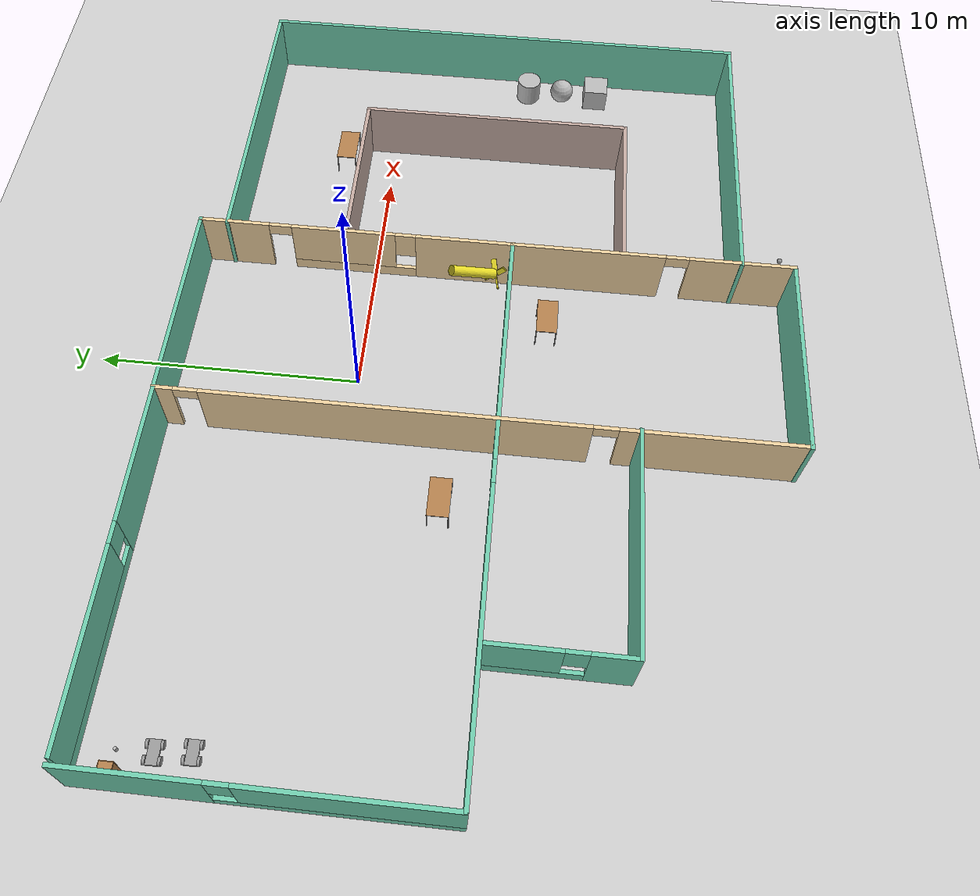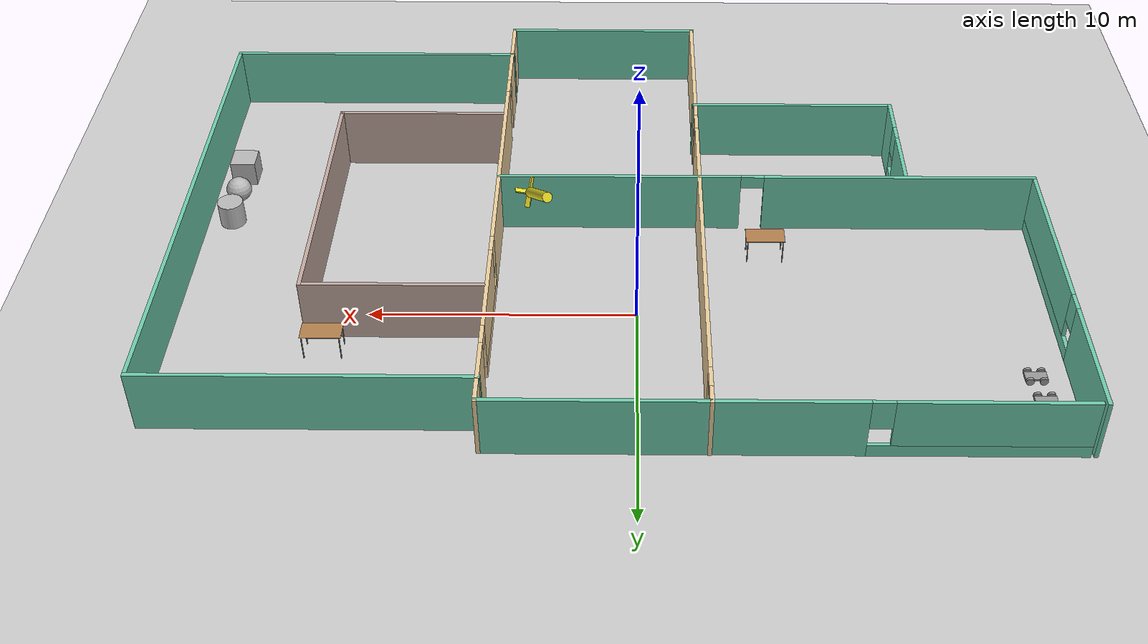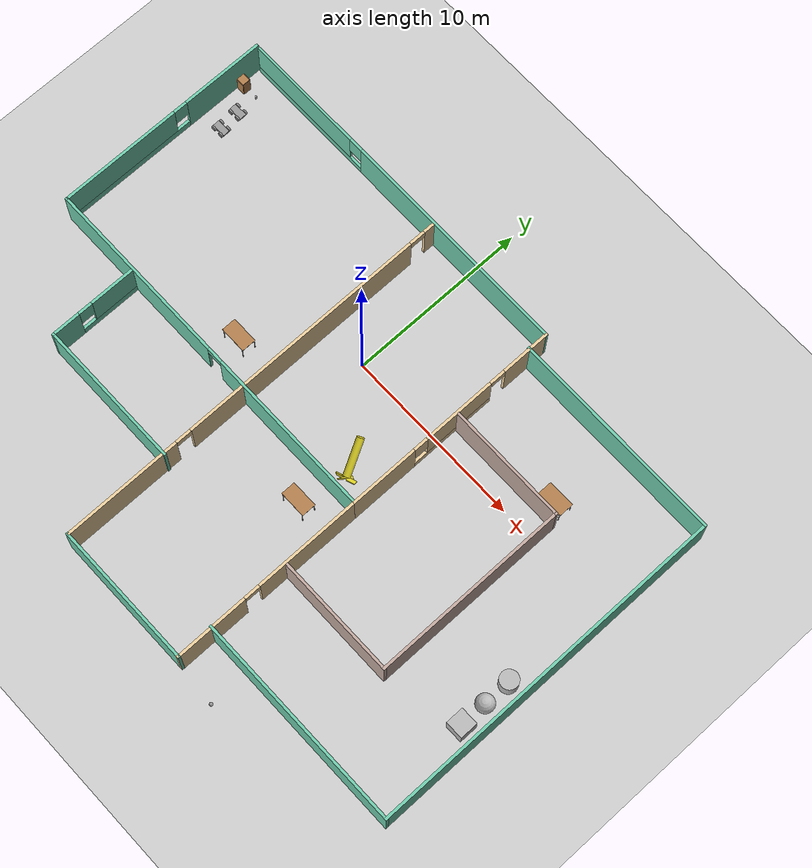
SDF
<sdf version="1.6">
 <world name="default">
  <plugin name="welcome" filename="libwelcome.so"/>
  <light name="sun" type="directional">
   <pose>0 0 10 0 -0 0</pose>
   <diffuse>0.8 0.8 0.8 1</diffuse>
   <specular>0.2 0.2 0.2 1</specular>
   <attenuation>
    <range>1000</range>
    <constant>0.9</constant>
    <linear>0.01</linear>
    <quadratic>0.001</quadratic>
   </attenuation>
   <direction>-0.5 0.1 -0.9</direction>
  </light>
  <model name="ground_plane">
   <static>1</static>
   <link name="link">
    <collision name="collision">
     <geometry><plane><normal>0 0 1</normal><size>100 100</size></plane></geometry>
     <surface>
      <contact><collide_bitmask>65535</collide_bitmask></contact>
      <friction><ode><mu>100</mu><mu2>50</mu2></ode></friction>
     </surface>
    </collision>
    <visual name="visual">
     <cast_shadows>0</cast_shadows>
     <geometry><plane><normal>0 0 1</normal><size>100 100</size></plane></geometry>
     <material>
      <script><uri>file://media/materials/scripts/gazebo.material</uri><name>Gazebo/Grey</name></script>
     </material>
    </visual>
   </link>
  </model>
  <gravity>0 0 -9.8</gravity>
  <magnetic_field>6e-06 2.3e-05 -4.2e-05</magnetic_field>
  <atmosphere type="adiabatic"/>
  <physics name="default_physics" default="0" type="ode">
   <max_step_size>0.001</max_step_size>
   <real_time_factor>1</real_time_factor>
   <real_time_update_rate>1000</real_time_update_rate>
  </physics>
  <scene><ambient>0.4 0.4 0.4 1</ambient><background>0.7 0.7 0.7 1</background><shadows>1</shadows></scene>
  <spherical_coordinates>
   <surface_model>EARTH_WGS84</surface_model>
   <latitude_deg>0</latitude_deg>
   <longitude_deg>0</longitude_deg>
   <elevation>0</elevation>
   <heading_deg>0</heading_deg>
  </spherical_coordinates>
  <model name="Building">
   <pose>0.87528 -4.65541 0 0 -0 0</pose>
   <link name="Wall_10">
    <pose>4.52008 5.41728 0 0 -0 1.5708</pose>
    <visual name="Wall_10_Visual_0">
     <pose>-4.3118 0 1.25 0 -0 0</pose>
     <geometry><box><size>3.8764 0.15 2.5</size></box></geometry>
     <material>
      <script><uri>file://media/materials/scripts/gazebo.material</uri><name>Gazebo/Grey</name></script>
      <ambient>0.921569 0.807843 0.615686 1</ambient>
     </material>
     <meta><layer>0</layer></meta>
    </visual>
    <collision name="Wall_10_Collision_0">
     <geometry><box><size>3.8764 0.15 2.5</size></box></geometry>
     <pose>-4.3118 0 1.25 0 -0 0</pose>
    </collision>
    <visual name="Wall_10_Visual_1">
     <pose>4.845 0 1.25 0 -0 0</pose>
     <geometry><box><size>2.80999 0.15 2.5</size></box></geometry>
     <material>
      <script><uri>file://media/materials/scripts/gazebo.material</uri><name>Gazebo/Grey</name></script>
      <ambient>0.921569 0.807843 0.615686 1</ambient>
     </material>
     <meta><layer>0</layer></meta>
    </visual>
    <collision name="Wall_10_Collision_1">
     <geometry><box><size>2.80999 0.15 2.5</size></box></geometry>
     <pose>4.845 0 1.25 0 -0 0</pose>
    </collision>
    <visual name="Wall_10_Visual_2">
     <pose>0.083203 0 0.25 0 -0 0</pose>
     <geometry><box><size>4.91361 0.15 0.5</size></box></geometry>
     <material>
      <script><uri>file://media/materials/scripts/gazebo.material</uri><name>Gazebo/Grey</name></script>
      <ambient>0.921569 0.807843 0.615686 1</ambient>
     </material>
     <meta><layer>0</layer></meta>
    </visual>
    <collision name="Wall_10_Collision_2">
     <geometry><box><size>4.91361 0.15 0.5</size></box></geometry>
     <pose>0.083203 0 0.25 0 -0 0</pose>
    </collision>
    <visual name="Wall_10_Visual_3">
     <pose>0.483203 0 1.5 0 -0 0</pose>
     <geometry><box><size>4.11361 0.15 2</size></box></geometry>
     <material>
      <script><uri>file://media/materials/scripts/gazebo.material</uri><name>Gazebo/Grey</name></script>
      <ambient>0.921569 0.807843 0.615686 1</ambient>
     </material>
     <meta><layer>0</layer></meta>
    </visual>
    <collision name="Wall_10_Collision_3">
     <geometry><box><size>4.11361 0.15 2</size></box></geometry>
     <pose>0.483203 0 1.5 0 -0 0</pose>
    </collision>
    <visual name="Wall_10_Visual_4">
     <pose>-1.9736 0 1.9 0 -0 0</pose>
     <geometry><box><size>0.8 0.15 1.2</size></box></geometry>
     <material>
      <script><uri>file://media/materials/scripts/gazebo.material</uri><name>Gazebo/Grey</name></script>
      <ambient>0.921569 0.807843 0.615686 1</ambient>
     </material>
     <meta><layer>0</layer></meta>
    </visual>
    <collision name="Wall_10_Collision_4">
     <geometry><box><size>0.8 0.15 1.2</size></box></geometry>
     <pose>-1.9736 0 1.9 0 -0 0</pose>
    </collision>
    <visual name="Wall_10_Visual_5">
     <pose>2.99001 0 2.25 0 -0 0</pose>
     <geometry><box><size>0.9 0.15 0.5</size></box></geometry>
     <material>
      <script><uri>file://media/materials/scripts/gazebo.material</uri><name>Gazebo/Grey</name></script>
      <ambient>0.921569 0.807843 0.615686 1</ambient>
     </material>
     <meta><layer>0</layer></meta>
    </visual>
    <collision name="Wall_10_Collision_5">
     <geometry><box><size>0.9 0.15 0.5</size></box></geometry>
     <pose>2.99001 0 2.25 0 -0 0</pose>
    </collision>
   </link>
   <link name="Wall_11">
    <pose>-5.77992 11.5923 0 0 -0 3.14159</pose>
    <visual name="Wall_11_Visual_0">
     <pose>-3.80191 0 1.25 0 -0 0</pose>
     <geometry><box><size>13.1462 0.15 2.5</size></box></geometry>
     <material>
      <script><uri>file://media/materials/scripts/gazebo.material</uri><name>Gazebo/Grey</name></script>
      <ambient>0.435294 0.796078 0.67451 1</ambient>
     </material>
     <meta><layer>0</layer></meta>
    </visual>
    <collision name="Wall_11_Collision_0">
     <geometry><box><size>13.1462 0.15 2.5</size></box></geometry>
     <pose>-3.80191 0 1.25 0 -0 0</pose>
    </collision>
    <visual name="Wall_11_Visual_1">
     <pose>6.57309 0 0.25 0 -0 0</pose>
     <geometry><box><size>7.60381 0.15 0.5</size></box></geometry>
     <material>
      <script><uri>file://media/materials/scripts/gazebo.material</uri><name>Gazebo/Grey</name></script>
      <ambient>0.435294 0.796078 0.67451 1</ambient>
     </material>
     <meta><layer>0</layer></meta>
    </visual>
    <collision name="Wall_11_Collision_1">
     <geometry><box><size>7.60381 0.15 0.5</size></box></geometry>
     <pose>6.57309 0 0.25 0 -0 0</pose>
    </collision>
    <visual name="Wall_11_Visual_2">
     <pose>6.97309 0 1.5 0 -0 0</pose>
     <geometry><box><size>6.80381 0.15 2</size></box></geometry>
     <material>
      <script><uri>file://media/materials/scripts/gazebo.material</uri><name>Gazebo/Grey</name></script>
      <ambient>0.435294 0.796078 0.67451 1</ambient>
     </material>
     <meta><layer>0</layer></meta>
    </visual>
    <collision name="Wall_11_Collision_2">
     <geometry><box><size>6.80381 0.15 2</size></box></geometry>
     <pose>6.97309 0 1.5 0 -0 0</pose>
    </collision>
    <visual name="Wall_11_Visual_3">
     <pose>3.17119 0 1.9 0 -0 0</pose>
     <geometry><box><size>0.8 0.15 1.2</size></box></geometry>
     <material>
      <script><uri>file://media/materials/scripts/gazebo.material</uri><name>Gazebo/Grey</name></script>
      <ambient>0.435294 0.796078 0.67451 1</ambient>
     </material>
     <meta><layer>0</layer></meta>
    </visual>
    <collision name="Wall_11_Collision_3">
     <geometry><box><size>0.8 0.15 1.2</size></box></geometry>
     <pose>3.17119 0 1.9 0 -0 0</pose>
    </collision>
   </link>
   <link name="Wall_13">
    <pose>-3.30365 0.032723 0 0 0 -1.5708</pose>
    <visual name="Wall_13_Visual_0">
     <pose>-11.2544 0 1.25 0 -0 0</pose>
     <geometry><box><size>0.791174 0.15 2.5</size></box></geometry>
     <material>
      <script><uri>file://media/materials/scripts/gazebo.material</uri><name>Gazebo/Grey</name></script>
      <ambient>0.921569 0.807843 0.615686 1</ambient>
     </material>
     <meta><layer>0</layer></meta>
    </visual>
    <collision name="Wall_13_Collision_0">
     <geometry><box><size>0.791174 0.15 2.5</size></box></geometry>
     <pose>-11.2544 0 1.25 0 -0 0</pose>
    </collision>
    <visual name="Wall_13_Visual_1">
     <pose>-2.92273 0 1.25 0 -0 0</pose>
     <geometry><box><size>14.0722 0.15 2.5</size></box></geometry>
     <material>
      <script><uri>file://media/materials/scripts/gazebo.material</uri><name>Gazebo/Grey</name></script>
      <ambient>0.921569 0.807843 0.615686 1</ambient>
     </material>
     <meta><layer>0</layer></meta>
    </visual>
    <collision name="Wall_13_Collision_1">
     <geometry><box><size>14.0722 0.15 2.5</size></box></geometry>
     <pose>-2.92273 0 1.25 0 -0 0</pose>
    </collision>
    <visual name="Wall_13_Visual_2">
     <pose>8.33168 0 1.25 0 -0 0</pose>
     <geometry><box><size>6.63663 0.15 2.5</size></box></geometry>
     <material>
      <script><uri>file://media/materials/scripts/gazebo.material</uri><name>Gazebo/Grey</name></script>
      <ambient>0.921569 0.807843 0.615686 1</ambient>
     </material>
     <meta><layer>0</layer></meta>
    </visual>
    <collision name="Wall_13_Collision_2">
     <geometry><box><size>6.63663 0.15 2.5</size></box></geometry>
     <pose>8.33168 0 1.25 0 -0 0</pose>
    </collision>
    <visual name="Wall_13_Visual_3">
     <pose>-10.4088 0 2.25 0 -0 0</pose>
     <geometry><box><size>0.9 0.15 0.5</size></box></geometry>
     <material>
      <script><uri>file://media/materials/scripts/gazebo.material</uri><name>Gazebo/Grey</name></script>
      <ambient>0.921569 0.807843 0.615686 1</ambient>
     </material>
     <meta><layer>0</layer></meta>
    </visual>
    <collision name="Wall_13_Collision_3">
     <geometry><box><size>0.9 0.15 0.5</size></box></geometry>
     <pose>-10.4088 0 2.25 0 -0 0</pose>
    </collision>
    <visual name="Wall_13_Visual_4">
     <pose>4.56337 0 2.25 0 -0 0</pose>
     <geometry><box><size>0.9 0.15 0.5</size></box></geometry>
     <material>
      <script><uri>file://media/materials/scripts/gazebo.material</uri><name>Gazebo/Grey</name></script>
      <ambient>0.921569 0.807843 0.615686 1</ambient>
     </material>
     <meta><layer>0</layer></meta>
    </visual>
    <collision name="Wall_13_Collision_4">
     <geometry><box><size>0.9 0.15 0.5</size></box></geometry>
     <pose>4.56337 0 2.25 0 -0 0</pose>
    </collision>
   </link>
   <link name="Wall_20">
    <pose>4.52008 -6.18272 0 0 0 -1.5708</pose>
    <visual name="Wall_20_Visual_0">
     <pose>-2.49911 0 1.25 0 -0 0</pose>
     <geometry><box><size>6.00178 0.15 2.5</size></box></geometry>
     <material>
      <script><uri>file://media/materials/scripts/gazebo.material</uri><name>Gazebo/Grey</name></script>
      <ambient>0.921569 0.807843 0.615686 1</ambient>
     </material>
     <meta><layer>0</layer></meta>
    </visual>
    <collision name="Wall_20_Collision_0">
     <geometry><box><size>6.00178 0.15 2.5</size></box></geometry>
     <pose>-2.49911 0 1.25 0 -0 0</pose>
    </collision>
    <visual name="Wall_20_Visual_1">
     <pose>3.45089 0 1.25 0 -0 0</pose>
     <geometry><box><size>4.09822 0.15 2.5</size></box></geometry>
     <material>
      <script><uri>file://media/materials/scripts/gazebo.material</uri><name>Gazebo/Grey</name></script>
      <ambient>0.921569 0.807843 0.615686 1</ambient>
     </material>
     <meta><layer>0</layer></meta>
    </visual>
    <collision name="Wall_20_Collision_1">
     <geometry><box><size>4.09822 0.15 2.5</size></box></geometry>
     <pose>3.45089 0 1.25 0 -0 0</pose>
    </collision>
    <visual name="Wall_20_Visual_2">
     <pose>0.951781 0 2.25 0 -0 0</pose>
     <geometry><box><size>0.9 0.15 0.5</size></box></geometry>
     <material>
      <script><uri>file://media/materials/scripts/gazebo.material</uri><name>Gazebo/Grey</name></script>
      <ambient>0.921569 0.807843 0.615686 1</ambient>
     </material>
     <meta><layer>0</layer></meta>
    </visual>
    <collision name="Wall_20_Collision_2">
     <geometry><box><size>0.9 0.15 0.5</size></box></geometry>
     <pose>0.951781 0 2.25 0 -0 0</pose>
    </collision>
   </link>
   <link name="Wall_21">
    <collision name="Wall_21_Collision">
     <geometry><box><size>8 0.15 2.5</size></box></geometry>
     <pose>0 0 1.25 0 -0 0</pose>
    </collision>
    <visual name="Wall_21_Visual">
     <pose>0 0 1.25 0 -0 0</pose>
     <geometry><box><size>8 0.15 2.5</size></box></geometry>
     <material>
      <script><uri>file://media/materials/scripts/gazebo.material</uri><name>Gazebo/Grey</name></script>
      <ambient>0.435294 0.796078 0.67451 1</ambient>
     </material>
     <meta><layer>0</layer></meta>
    </visual>
    <pose>0.595079 -11.6077 0 0 -0 3.14159</pose>
   </link>
   <link name="Wall_23">
    <collision name="Wall_23_Collision">
     <geometry><box><size>8.25 0.15 2.5</size></box></geometry>
     <pose>0 0 1.25 0 -0 0</pose>
    </collision>
    <visual name="Wall_23_Visual">
     <pose>0 0 1.25 0 -0 0</pose>
     <geometry><box><size>8.25 0.15 2.5</size></box></geometry>
     <material>
      <script><uri>file://media/materials/scripts/gazebo.material</uri><name>Gazebo/Grey</name></script>
      <ambient>0.435294 0.796078 0.67451 1</ambient>
     </material>
     <meta><layer>0</layer></meta>
    </visual>
    <pose>-7.30029 -5.76127 0 0 -0 3.14159</pose>
   </link>
   <link name="Wall_24">
    <pose>-11.3503 -3.33627 0 0 -0 1.5708</pose>
    <visual name="Wall_24_Visual_0">
     <pose>-1.68102 0 1.25 0 -0 0</pose>
     <geometry><box><size>1.63796 0.15 2.5</size></box></geometry>
     <material>
      <script><uri>file://media/materials/scripts/gazebo.material</uri><name>Gazebo/Grey</name></script>
      <ambient>0.435294 0.796078 0.67451 1</ambient>
     </material>
     <meta><layer>0</layer></meta>
    </visual>
    <collision name="Wall_24_Collision_0">
     <geometry><box><size>1.63796 0.15 2.5</size></box></geometry>
     <pose>-1.68102 0 1.25 0 -0 0</pose>
    </collision>
    <visual name="Wall_24_Visual_1">
     <pose>0.818982 0 0.25 0 -0 0</pose>
     <geometry><box><size>3.36204 0.15 0.5</size></box></geometry>
     <material>
      <script><uri>file://media/materials/scripts/gazebo.material</uri><name>Gazebo/Grey</name></script>
      <ambient>0.435294 0.796078 0.67451 1</ambient>
     </material>
     <meta><layer>0</layer></meta>
    </visual>
    <collision name="Wall_24_Collision_1">
     <geometry><box><size>3.36204 0.15 0.5</size></box></geometry>
     <pose>0.818982 0 0.25 0 -0 0</pose>
    </collision>
    <visual name="Wall_24_Visual_2">
     <pose>1.21898 0 1.5 0 -0 0</pose>
     <geometry><box><size>2.56203 0.15 2</size></box></geometry>
     <material>
      <script><uri>file://media/materials/scripts/gazebo.material</uri><name>Gazebo/Grey</name></script>
      <ambient>0.435294 0.796078 0.67451 1</ambient>
     </material>
     <meta><layer>0</layer></meta>
    </visual>
    <collision name="Wall_24_Collision_2">
     <geometry><box><size>2.56203 0.15 2</size></box></geometry>
     <pose>1.21898 0 1.5 0 -0 0</pose>
    </collision>
    <visual name="Wall_24_Visual_3">
     <pose>-0.462035 0 1.9 0 -0 0</pose>
     <geometry><box><size>0.8 0.15 1.2</size></box></geometry>
     <material>
      <script><uri>file://media/materials/scripts/gazebo.material</uri><name>Gazebo/Grey</name></script>
      <ambient>0.435294 0.796078 0.67451 1</ambient>
     </material>
     <meta><layer>0</layer></meta>
    </visual>
    <collision name="Wall_24_Collision_3">
     <geometry><box><size>0.8 0.15 1.2</size></box></geometry>
     <pose>-0.462035 0 1.9 0 -0 0</pose>
    </collision>
   </link>
   <link name="Wall_27">
    <collision name="Wall_27_Collision">
     <geometry><box><size>12 0.15 2.5</size></box></geometry>
     <pose>0 0 1.25 0 -0 0</pose>
    </collision>
    <visual name="Wall_27_Visual">
     <pose>0 0 1.25 0 -0 0</pose>
     <geometry><box><size>12 0.15 2.5</size></box></geometry>
     <material>
      <script><uri>file://media/materials/scripts/gazebo.material</uri><name>Gazebo/Grey</name></script>
      <ambient>0.435294 0.796078 0.67451 1</ambient>
     </material>
     <meta><layer>0</layer></meta>
    </visual>
    <pose>10.4049 10.5129 0 0 -0 0</pose>
   </link>
   <link name="Wall_28">
    <collision name="Wall_28_Collision">
     <geometry><box><size>20.25 0.15 2.5</size></box></geometry>
     <pose>0 0 1.25 0 -0 0</pose>
    </collision>
    <visual name="Wall_28_Visual">
     <pose>0 0 1.25 0 -0 0</pose>
     <geometry><box><size>20.25 0.15 2.5</size></box></geometry>
     <material>
      <script><uri>file://media/materials/scripts/gazebo.material</uri><name>Gazebo/Grey</name></script>
      <ambient>0.435294 0.796078 0.67451 1</ambient>
     </material>
     <meta><layer>0</layer></meta>
    </visual>
    <pose>16.3299 0.46285 0 0 0 -1.5708</pose>
   </link>
   <link name="Wall_29">
    <collision name="Wall_29_Collision">
     <geometry><box><size>12 0.15 2.5</size></box></geometry>
     <pose>0 0 1.25 0 -0 0</pose>
    </collision>
    <visual name="Wall_29_Visual">
     <pose>0 0 1.25 0 -0 0</pose>
     <geometry><box><size>12 0.15 2.5</size></box></geometry>
     <material>
      <script><uri>file://media/materials/scripts/gazebo.material</uri><name>Gazebo/Grey</name></script>
      <ambient>0.435294 0.796078 0.67451 1</ambient>
     </material>
     <meta><layer>0</layer></meta>
    </visual>
    <pose>10.4049 -9.58715 0 0 -0 3.14159</pose>
   </link>
   <link name="Wall_31">
    <collision name="Wall_31_Collision">
     <geometry><box><size>6.75 0.15 2.5</size></box></geometry>
     <pose>0 0 1.25 0 -0 0</pose>
    </collision>
    <visual name="Wall_31_Visual">
     <pose>0 0 1.25 0 -0 0</pose>
     <geometry><box><size>6.75 0.15 2.5</size></box></geometry>
     <material>
      <script><uri>file://media/materials/scripts/gazebo.material</uri><name>Gazebo/Grey</name></script>
      <ambient>0.760784 0.662745 0.627451 1</ambient>
     </material>
     <meta><layer>0</layer></meta>
    </visual>
    <pose>7.94855 5.79336 0 0 -0 0</pose>
   </link>
   <link name="Wall_32">
    <collision name="Wall_32_Collision">
     <geometry><box><size>11 0.15 2.5</size></box></geometry>
     <pose>0 0 1.25 0 -0 0</pose>
    </collision>
    <visual name="Wall_32_Visual">
     <pose>0 0 1.25 0 -0 0</pose>
     <geometry><box><size>11 0.15 2.5</size></box></geometry>
     <material>
      <script><uri>file://media/materials/scripts/gazebo.material</uri><name>Gazebo/Grey</name></script>
      <ambient>0.760784 0.662745 0.627451 1</ambient>
     </material>
     <meta><layer>0</layer></meta>
    </visual>
    <pose>11.2485 0.368355 0 0 0 -1.5708</pose>
   </link>
   <link name="Wall_33">
    <collision name="Wall_33_Collision">
     <geometry><box><size>6.75 0.15 2.5</size></box></geometry>
     <pose>0 0 1.25 0 -0 0</pose>
    </collision>
    <visual name="Wall_33_Visual">
     <pose>0 0 1.25 0 -0 0</pose>
     <geometry><box><size>6.75 0.15 2.5</size></box></geometry>
     <material>
      <script><uri>file://media/materials/scripts/gazebo.material</uri><name>Gazebo/Grey</name></script>
      <ambient>0.760784 0.662745 0.627451 1</ambient>
     </material>
     <meta><layer>0</layer></meta>
    </visual>
    <pose>7.94855 -5.05664 0 0 -0 3.14159</pose>
   </link>
   <link name="Wall_8">
    <pose>-16.3299 5.41728 0 0 0 -1.5708</pose>
    <visual name="Wall_8_Visual_0">
     <pose>-3.88424 0 1.25 0 -0 0</pose>
     <geometry><box><size>4.73152 0.15 2.5</size></box></geometry>
     <material>
      <script><uri>file://media/materials/scripts/gazebo.material</uri><name>Gazebo/Grey</name></script>
      <ambient>0.435294 0.796078 0.67451 1</ambient>
     </material>
     <meta><layer>0</layer></meta>
    </visual>
    <collision name="Wall_8_Collision_0">
     <geometry><box><size>4.73152 0.15 2.5</size></box></geometry>
     <pose>-3.88424 0 1.25 0 -0 0</pose>
    </collision>
    <visual name="Wall_8_Visual_1">
     <pose>2.36576 0 0.25 0 -0 0</pose>
     <geometry><box><size>7.76848 0.15 0.5</size></box></geometry>
     <material>
      <script><uri>file://media/materials/scripts/gazebo.material</uri><name>Gazebo/Grey</name></script>
      <ambient>0.435294 0.796078 0.67451 1</ambient>
     </material>
     <meta><layer>0</layer></meta>
    </visual>
    <collision name="Wall_8_Collision_1">
     <geometry><box><size>7.76848 0.15 0.5</size></box></geometry>
     <pose>2.36576 0 0.25 0 -0 0</pose>
    </collision>
    <visual name="Wall_8_Visual_2">
     <pose>2.76576 0 1.5 0 -0 0</pose>
     <geometry><box><size>6.96848 0.15 2</size></box></geometry>
     <material>
      <script><uri>file://media/materials/scripts/gazebo.material</uri><name>Gazebo/Grey</name></script>
      <ambient>0.435294 0.796078 0.67451 1</ambient>
     </material>
     <meta><layer>0</layer></meta>
    </visual>
    <collision name="Wall_8_Collision_2">
     <geometry><box><size>6.96848 0.15 2</size></box></geometry>
     <pose>2.76576 0 1.5 0 -0 0</pose>
    </collision>
    <visual name="Wall_8_Visual_3">
     <pose>-1.11848 0 1.9 0 -0 0</pose>
     <geometry><box><size>0.8 0.15 1.2</size></box></geometry>
     <material>
      <script><uri>file://media/materials/scripts/gazebo.material</uri><name>Gazebo/Grey</name></script>
      <ambient>0.435294 0.796078 0.67451 1</ambient>
     </material>
     <meta><layer>0</layer></meta>
    </visual>
    <collision name="Wall_8_Collision_3">
     <geometry><box><size>0.8 0.15 1.2</size></box></geometry>
     <pose>-1.11848 0 1.9 0 -0 0</pose>
    </collision>
   </link>
   <link name="Wall_9">
    <pose>-5.90492 -0.757723 0 0 -0 0</pose>
    <visual name="Wall_9_Visual_0">
     <pose>-5.20794 0 1.25 0 -0 0</pose>
     <geometry><box><size>10.5841 0.15 2.5</size></box></geometry>
     <material>
      <script><uri>file://media/materials/scripts/gazebo.material</uri><name>Gazebo/Grey</name></script>
      <ambient>0.435294 0.796078 0.67451 1</ambient>
     </material>
     <meta><layer>0</layer></meta>
    </visual>
    <collision name="Wall_9_Collision_0">
     <geometry><box><size>10.5841 0.15 2.5</size></box></geometry>
     <pose>-5.20794 0 1.25 0 -0 0</pose>
    </collision>
    <visual name="Wall_9_Visual_1">
     <pose>5.74206 0 1.25 0 -0 0</pose>
     <geometry><box><size>9.51588 0.15 2.5</size></box></geometry>
     <material>
      <script><uri>file://media/materials/scripts/gazebo.material</uri><name>Gazebo/Grey</name></script>
      <ambient>0.435294 0.796078 0.67451 1</ambient>
     </material>
     <meta><layer>0</layer></meta>
    </visual>
    <collision name="Wall_9_Collision_1">
     <geometry><box><size>9.51588 0.15 2.5</size></box></geometry>
     <pose>5.74206 0 1.25 0 -0 0</pose>
    </collision>
    <visual name="Wall_9_Visual_2">
     <pose>0.53412 0 2.25 0 -0 0</pose>
     <geometry><box><size>0.9 0.15 0.5</size></box></geometry>
     <material>
      <script><uri>file://media/materials/scripts/gazebo.material</uri><name>Gazebo/Grey</name></script>
      <ambient>0.435294 0.796078 0.67451 1</ambient>
     </material>
     <meta><layer>0</layer></meta>
    </visual>
    <collision name="Wall_9_Collision_2">
     <geometry><box><size>0.9 0.15 0.5</size></box></geometry>
     <pose>0.53412 0 2.25 0 -0 0</pose>
    </collision>
   </link>
   <static>1</static>
  </model>
  <model name="Car">
   <link name="link_0">
    <inertial>
     <mass>1</mass>
     <inertia>
      <ixx>0.166667</ixx>
      <ixy>0</ixy>
      <ixz>0</ixz>
      <iyy>0.166667</iyy>
      <iyz>0</iyz>
      <izz>0.166667</izz>
     </inertia>
    </inertial>
    <visual name="visual">
     <geometry><box><size>0.8 0.4 0.1</size></box></geometry>
     <material>
      <lighting>1</lighting>
      <script><uri>file://media/materials/scripts/gazebo.material</uri><name>Gazebo/Grey</name></script>
      <shader type="pixel"><normal_map>__default__</normal_map></shader>
      <ambient>0.3 0.3 0.3 1</ambient>
      <diffuse>0.7 0.7 0.7 1</diffuse>
      <specular>0.01 0.01 0.01 1</specular>
      <emissive>0 0 0 1</emissive>
     </material>
    </visual>
    <collision name="collision">
     <geometry><box><size>0.8 0.4 0.05</size></box></geometry>
     <surface>
      <friction>
       <ode><mu>1</mu><mu2>1</mu2><fdir1>0 0 0</fdir1><slip1>0</slip1><slip2>0</slip2></ode>
       <torsional>
        <coefficient>1</coefficient>
        <patch_radius>0</patch_radius>
        <surface_radius>0</surface_radius>
        <use_patch_radius>1</use_patch_radius>
        <ode><slip>0</slip></ode>
       </torsional>
      </friction>
      <bounce><restitution_coefficient>0</restitution_coefficient><threshold>1e+06</threshold></bounce>
      <contact>
       <collide_without_contact>0</collide_without_contact>
       <collide_without_contact_bitmask>1</collide_without_contact_bitmask>
       <collide_bitmask>1</collide_bitmask>
       <ode>
        <soft_cfm>0</soft_cfm>
        <soft_erp>0.2</soft_erp>
        <kp>1e+13</kp>
        <kd>1</kd>
        <max_vel>0.01</max_vel>
        <min_depth>0</min_depth>
       </ode>
       <bullet>
        <split_impulse>1</split_impulse>
        <split_impulse_penetration_threshold>-0.01</split_impulse_penetration_threshold>
        <soft_cfm>0</soft_cfm>
        <soft_erp>0.2</soft_erp>
        <kp>1e+13</kp>
        <kd>1</kd>
       </bullet>
      </contact>
     </surface>
    </collision>
   </link>
   <link name="link_1">
    <pose>-0.25 -0.250014 0 1.5707 -0 0</pose>
    <inertial>
     <mass>1</mass>
     <inertia><ixx>0.145833</ixx><ixy>0</ixy><ixz>0</ixz><iyy>0.145833</iyy><iyz>0</iyz><izz>0.125</izz></inertia>
    </inertial>
    <visual name="visual">
     <geometry><cylinder><radius>0.15</radius><length>0.1</length></cylinder></geometry>
     <material>
      <lighting>1</lighting>
      <script><uri>file://media/materials/scripts/gazebo.material</uri><name>Gazebo/Grey</name></script>
      <shader type="pixel"><normal_map>__default__</normal_map></shader>
      <ambient>0.3 0.3 0.3 1</ambient>
      <diffuse>0.7 0.7 0.7 1</diffuse>
      <specular>0.01 0.01 0.01 1</specular>
      <emissive>0 0 0 1</emissive>
     </material>
    </visual>
    <collision name="collision">
     <geometry><cylinder><radius>0.15</radius><length>0.1</length></cylinder></geometry>
     <surface>
      <friction>
       <ode><mu>1</mu><mu2>1</mu2><fdir1>0 0 0</fdir1><slip1>0</slip1><slip2>0</slip2></ode>
       <torsional>
        <coefficient>1</coefficient>
        <patch_radius>0</patch_radius>
        <surface_radius>0</surface_radius>
        <use_patch_radius>1</use_patch_radius>
        <ode><slip>0</slip></ode>
       </torsional>
      </friction>
      <bounce><restitution_coefficient>0</restitution_coefficient><threshold>1e+06</threshold></bounce>
      <contact>
       <collide_without_contact>0</collide_without_contact>
       <collide_without_contact_bitmask>1</collide_without_contact_bitmask>
       <collide_bitmask>1</collide_bitmask>
       <ode>
        <soft_cfm>0</soft_cfm>
        <soft_erp>0.2</soft_erp>
        <kp>1e+13</kp>
        <kd>1</kd>
        <max_vel>0.01</max_vel>
        <min_depth>0</min_depth>
       </ode>
       <bullet>
        <split_impulse>1</split_impulse>
        <split_impulse_penetration_threshold>-0.01</split_impulse_penetration_threshold>
        <soft_cfm>0</soft_cfm>
        <soft_erp>0.2</soft_erp>
        <kp>1e+13</kp>
        <kd>1</kd>
       </bullet>
      </contact>
     </surface>
    </collision>
   </link>
   <link name="link_1_clone">
    <pose>-0.25 0.250014 0 1.5707 -0 0</pose>
    <inertial>
     <mass>1</mass>
     <inertia><ixx>0.145833</ixx><ixy>0</ixy><ixz>0</ixz><iyy>0.145833</iyy><iyz>0</iyz><izz>0.125</izz></inertia>
    </inertial>
    <visual name="visual">
     <geometry><cylinder><radius>0.15</radius><length>0.1</length></cylinder></geometry>
     <material>
      <lighting>1</lighting>
      <script><uri>file://media/materials/scripts/gazebo.material</uri><name>Gazebo/Grey</name></script>
      <shader type="pixel"><normal_map>__default__</normal_map></shader>
      <ambient>0.3 0.3 0.3 1</ambient>
      <diffuse>0.7 0.7 0.7 1</diffuse>
      <specular>0.01 0.01 0.01 1</specular>
      <emissive>0 0 0 1</emissive>
     </material>
    </visual>
    <collision name="collision">
     <geometry><cylinder><radius>0.15</radius><length>0.1</length></cylinder></geometry>
     <surface>
      <friction>
       <ode><mu>1</mu><mu2>1</mu2><fdir1>0 0 0</fdir1><slip1>0</slip1><slip2>0</slip2></ode>
       <torsional>
        <coefficient>1</coefficient>
        <patch_radius>0</patch_radius>
        <surface_radius>0</surface_radius>
        <use_patch_radius>1</use_patch_radius>
        <ode><slip>0</slip></ode>
       </torsional>
      </friction>
      <bounce><restitution_coefficient>0</restitution_coefficient><threshold>1e+06</threshold></bounce>
      <contact>
       <collide_without_contact>0</collide_without_contact>
       <collide_without_contact_bitmask>1</collide_without_contact_bitmask>
       <collide_bitmask>1</collide_bitmask>
       <ode>
        <soft_cfm>0</soft_cfm>
        <soft_erp>0.2</soft_erp>
        <kp>1e+13</kp>
        <kd>1</kd>
        <max_vel>0.01</max_vel>
        <min_depth>0</min_depth>
       </ode>
       <bullet>
        <split_impulse>1</split_impulse>
        <split_impulse_penetration_threshold>-0.01</split_impulse_penetration_threshold>
        <soft_cfm>0</soft_cfm>
        <soft_erp>0.2</soft_erp>
        <kp>1e+13</kp>
        <kd>1</kd>
       </bullet>
      </contact>
     </surface>
    </collision>
   </link>
   <link name="link_1_clone_clone">
    <pose>0.25 -0.250014 0 1.5707 -0 0</pose>
    <inertial>
     <mass>1</mass>
     <inertia><ixx>0.145833</ixx><ixy>0</ixy><ixz>0</ixz><iyy>0.145833</iyy><iyz>0</iyz><izz>0.125</izz></inertia>
    </inertial>
    <visual name="visual">
     <geometry><cylinder><radius>0.15</radius><length>0.1</length></cylinder></geometry>
     <material>
      <lighting>1</lighting>
      <script><uri>file://media/materials/scripts/gazebo.material</uri><name>Gazebo/Grey</name></script>
      <shader type="pixel"><normal_map>__default__</normal_map></shader>
      <ambient>0.3 0.3 0.3 1</ambient>
      <diffuse>0.7 0.7 0.7 1</diffuse>
      <specular>0.01 0.01 0.01 1</specular>
      <emissive>0 0 0 1</emissive>
     </material>
    </visual>
    <collision name="collision">
     <geometry><cylinder><radius>0.15</radius><length>0.1</length></cylinder></geometry>
     <surface>
      <friction>
       <ode><mu>1</mu><mu2>1</mu2><fdir1>0 0 0</fdir1><slip1>0</slip1><slip2>0</slip2></ode>
       <torsional>
        <coefficient>1</coefficient>
        <patch_radius>0</patch_radius>
        <surface_radius>0</surface_radius>
        <use_patch_radius>1</use_patch_radius>
        <ode><slip>0</slip></ode>
       </torsional>
      </friction>
      <bounce><restitution_coefficient>0</restitution_coefficient><threshold>1e+06</threshold></bounce>
      <contact>
       <collide_without_contact>0</collide_without_contact>
       <collide_without_contact_bitmask>1</collide_without_contact_bitmask>
       <collide_bitmask>1</collide_bitmask>
       <ode>
        <soft_cfm>0</soft_cfm>
        <soft_erp>0.2</soft_erp>
        <kp>1e+13</kp>
        <kd>1</kd>
        <max_vel>0.01</max_vel>
        <min_depth>0</min_depth>
       </ode>
       <bullet>
        <split_impulse>1</split_impulse>
        <split_impulse_penetration_threshold>-0.01</split_impulse_penetration_threshold>
        <soft_cfm>0</soft_cfm>
        <soft_erp>0.2</soft_erp>
        <kp>1e+13</kp>
        <kd>1</kd>
       </bullet>
      </contact>
     </surface>
    </collision>
   </link>
   <link name="link_1_clone_clone_0">
    <pose>0.25 0.250014 0 1.5707 -0 0</pose>
    <inertial>
     <mass>1</mass>
     <inertia><ixx>0.145833</ixx><ixy>0</ixy><ixz>0</ixz><iyy>0.145833</iyy><iyz>0</iyz><izz>0.125</izz></inertia>
    </inertial>
    <visual name="visual">
     <geometry><cylinder><radius>0.15</radius><length>0.1</length></cylinder></geometry>
     <material>
      <lighting>1</lighting>
      <script><uri>file://media/materials/scripts/gazebo.material</uri><name>Gazebo/Grey</name></script>
      <shader type="pixel"><normal_map>__default__</normal_map></shader>
      <ambient>0.3 0.3 0.3 1</ambient>
      <diffuse>0.7 0.7 0.7 1</diffuse>
      <specular>0.01 0.01 0.01 1</specular>
      <emissive>0 0 0 1</emissive>
     </material>
    </visual>
    <collision name="collision">
     <geometry><cylinder><radius>0.15</radius><length>0.1</length></cylinder></geometry>
     <surface>
      <friction>
       <ode><mu>1</mu><mu2>1</mu2><fdir1>0 0 0</fdir1><slip1>0</slip1><slip2>0</slip2></ode>
       <torsional>
        <coefficient>1</coefficient>
        <patch_radius>0</patch_radius>
        <surface_radius>0</surface_radius>
        <use_patch_radius>1</use_patch_radius>
        <ode><slip>0</slip></ode>
       </torsional>
      </friction>
      <bounce><restitution_coefficient>0</restitution_coefficient><threshold>1e+06</threshold></bounce>
      <contact>
       <collide_without_contact>0</collide_without_contact>
       <collide_without_contact_bitmask>1</collide_without_contact_bitmask>
       <collide_bitmask>1</collide_bitmask>
       <ode>
        <soft_cfm>0</soft_cfm>
        <soft_erp>0.2</soft_erp>
        <kp>1e+13</kp>
        <kd>1</kd>
        <max_vel>0.01</max_vel>
        <min_depth>0</min_depth>
       </ode>
       <bullet>
        <split_impulse>1</split_impulse>
        <split_impulse_penetration_threshold>-0.01</split_impulse_penetration_threshold>
        <soft_cfm>0</soft_cfm>
        <soft_erp>0.2</soft_erp>
        <kp>1e+13</kp>
        <kd>1</kd>
       </bullet>
      </contact>
     </surface>
    </collision>
   </link>
   <joint name="link_0_JOINT_1" type="revolute">
    <parent>link_0</parent>
    <child>link_1</child>
    <axis>
     <xyz>0 0 1</xyz>
     <use_parent_model_frame>0</use_parent_model_frame>
     <limit>
      <lower>-1.79769e+308</lower>
      <upper>1.79769e+308</upper>
      <effort>-1</effort>
      <velocity>-1</velocity>
     </limit>
     <dynamics>
      <spring_reference>0</spring_reference>
      <spring_stiffness>0</spring_stiffness>
      <damping>0</damping>
     </dynamics>
    </axis>
    <physics>
     <ode><limit><cfm>0</cfm><erp>0.2</erp></limit><suspension><cfm>0</cfm><erp>0.2</erp></suspension></ode>
    </physics>
   </joint>
   <joint name="link_0_JOINT_2" type="revolute">
    <parent>link_0</parent>
    <child>link_1_clone</child>
    <axis>
     <xyz>0 0 1</xyz>
     <use_parent_model_frame>0</use_parent_model_frame>
     <limit>
      <lower>-1.79769e+308</lower>
      <upper>1.79769e+308</upper>
      <effort>-1</effort>
      <velocity>-1</velocity>
     </limit>
     <dynamics>
      <spring_reference>0</spring_reference>
      <spring_stiffness>0</spring_stiffness>
      <damping>0</damping>
     </dynamics>
    </axis>
    <physics>
     <ode><limit><cfm>0</cfm><erp>0.2</erp></limit><suspension><cfm>0</cfm><erp>0.2</erp></suspension></ode>
    </physics>
   </joint>
   <joint name="link_0_JOINT_3" type="revolute">
    <parent>link_0</parent>
    <child>link_1_clone_clone</child>
    <axis>
     <xyz>0 0 1</xyz>
     <use_parent_model_frame>0</use_parent_model_frame>
     <limit>
      <lower>-1.79769e+308</lower>
      <upper>1.79769e+308</upper>
      <effort>-1</effort>
      <velocity>-1</velocity>
     </limit>
     <dynamics>
      <spring_reference>0</spring_reference>
      <spring_stiffness>0</spring_stiffness>
      <damping>0</damping>
     </dynamics>
    </axis>
    <physics>
     <ode><limit><cfm>0</cfm><erp>0.2</erp></limit><suspension><cfm>0</cfm><erp>0.2</erp></suspension></ode>
    </physics>
   </joint>
   <joint name="link_0_JOINT_4" type="revolute">
    <parent>link_0</parent>
    <child>link_1_clone_clone_0</child>
    <axis>
     <xyz>0 0 1</xyz>
     <use_parent_model_frame>0</use_parent_model_frame>
     <limit>
      <lower>-1.79769e+308</lower>
      <upper>1.79769e+308</upper>
      <effort>-1</effort>
      <velocity>-1</velocity>
     </limit>
     <dynamics>
      <spring_reference>0</spring_reference>
      <spring_stiffness>0</spring_stiffness>
      <damping>0</damping>
     </dynamics>
    </axis>
    <physics>
     <ode><limit><cfm>0</cfm><erp>0.2</erp></limit><suspension><cfm>0</cfm><erp>0.2</erp></suspension></ode>
    </physics>
   </joint>
   <static>0</static>
   <pose>-14.1618 3.25062 0.150005 5e-06 5e-06 0.017403</pose>
  </model>
  <model name="cabinet">
   <static>1</static>
   <link name="cabinet_bottom_plate">
    <inertial>
     <pose>0 0 -1 0 -0 0</pose>
     <inertia><ixx>2.05</ixx><ixy>0</ixy><ixz>0</ixz><iyy>2.05</iyy><iyz>0</iyz><izz>2.05</izz></inertia>
     <mass>25</mass>
    </inertial>
    <collision name="cabinet_bottom_plate_geom">
     <pose>0 0 0.01 0 -0 0</pose>
     <geometry><box><size>0.45 0.45 0.02</size></box></geometry>
    </collision>
    <visual name="cabinet_bottom_plate_geom_visual">
     <pose>0 0 0.01 0 -0 0</pose>
     <geometry><box><size>0.45 0.45 0.02</size></box></geometry>
     <material>
      <script><uri>file://media/materials/scripts/gazebo.material</uri><name>Gazebo/Wood</name></script>
     </material>
    </visual>
    <collision name="cabinet_bottom_plate_geom_cabinet_back_plate">
     <pose>0.235 0 0.51 0 -0 0</pose>
     <geometry><box><size>0.02 0.45 1.02</size></box></geometry>
    </collision>
    <visual name="cabinet_bottom_plate_geom_cabinet_back_plate_visual">
     <pose>0.235 0 0.51 0 -0 0</pose>
     <geometry><box><size>0.02 0.45 1.02</size></box></geometry>
     <material>
      <script><uri>file://media/materials/scripts/gazebo.material</uri><name>Gazebo/Wood</name></script>
     </material>
    </visual>
    <collision name="cabinet_bottom_plate_geom_cabinet_left_plate">
     <pose>0 0.235 0.51 0 -0 0</pose>
     <geometry><box><size>0.45 0.02 1.02</size></box></geometry>
    </collision>
    <visual name="cabinet_bottom_plate_geom_cabinet_left_plate_visual">
     <pose>0 0.235 0.51 0 -0 0</pose>
     <geometry><box><size>0.45 0.02 1.02</size></box></geometry>
     <material>
      <script><uri>file://media/materials/scripts/gazebo.material</uri><name>Gazebo/Wood</name></script>
     </material>
    </visual>
    <collision name="cabinet_bottom_plate_geom_cabinet_middle_plate">
     <pose>0 0 0.51 0 -0 0</pose>
     <geometry><box><size>0.45 0.45 0.02</size></box></geometry>
    </collision>
    <visual name="cabinet_bottom_plate_geom_cabinet_middle_plate_visual">
     <pose>0 0 0.51 0 -0 0</pose>
     <geometry><box><size>0.45 0.45 0.02</size></box></geometry>
     <material>
      <script><uri>file://media/materials/scripts/gazebo.material</uri><name>Gazebo/Wood</name></script>
     </material>
    </visual>
    <collision name="cabinet_bottom_plate_geom_cabinet_right_plate">
     <pose>0 -0.235 0.51 0 -0 0</pose>
     <geometry><box><size>0.45 0.02 1.02</size></box></geometry>
    </collision>
    <visual name="cabinet_bottom_plate_geom_cabinet_right_plate_visual">
     <pose>0 -0.235 0.51 0 -0 0</pose>
     <geometry><box><size>0.45 0.02 1.02</size></box></geometry>
     <material>
      <script><uri>file://media/materials/scripts/gazebo.material</uri><name>Gazebo/Wood</name></script>
     </material>
    </visual>
    <collision name="cabinet_bottom_plate_geom_cabinet_top_plate">
     <pose>0 0 1.01 0 -0 0</pose>
     <geometry><box><size>0.45 0.45 0.02</size></box></geometry>
    </collision>
    <visual name="cabinet_bottom_plate_geom_cabinet_top_plate_visual">
     <pose>0 0 1.01 0 -0 0</pose>
     <geometry><box><size>0.45 0.45 0.02</size></box></geometry>
     <material>
      <script><uri>file://media/materials/scripts/gazebo.material</uri><name>Gazebo/Wood</name></script>
     </material>
    </visual>
   </link>
   <pose>-15.105 5.6369 0 0 -0 0</pose>
  </model>
  <model name="table">
   <static>1</static>
   <link name="link">
    <collision name="surface">
     <pose>0 0 1 0 -0 0</pose>
     <geometry><box><size>1.5 0.8 0.03</size></box></geometry>
     <surface><friction><ode><mu>0.6</mu><mu2>0.6</mu2></ode></friction></surface>
    </collision>
    <visual name="visual1">
     <pose>0 0 1 0 -0 0</pose>
     <geometry><box><size>1.5 0.8 0.03</size></box></geometry>
     <material>
      <script><uri>file://media/materials/scripts/gazebo.material</uri><name>Gazebo/Wood</name></script>
     </material>
    </visual>
    <collision name="front_left_leg">
     <pose>0.68 0.38 0.5 0 -0 0</pose>
     <geometry><cylinder><radius>0.02</radius><length>1</length></cylinder></geometry>
    </collision>
    <visual name="front_left_leg">
     <pose>0.68 0.38 0.5 0 -0 0</pose>
     <geometry><cylinder><radius>0.02</radius><length>1</length></cylinder></geometry>
     <material>
      <script><uri>file://media/materials/scripts/gazebo.material</uri><name>Gazebo/Grey</name></script>
     </material>
    </visual>
    <collision name="front_right_leg">
     <pose>0.68 -0.38 0.5 0 -0 0</pose>
     <geometry><cylinder><radius>0.02</radius><length>1</length></cylinder></geometry>
    </collision>
    <visual name="front_right_leg">
     <pose>0.68 -0.38 0.5 0 -0 0</pose>
     <geometry><cylinder><radius>0.02</radius><length>1</length></cylinder></geometry>
     <material>
      <script><uri>file://media/materials/scripts/gazebo.material</uri><name>Gazebo/Grey</name></script>
     </material>
    </visual>
    <collision name="back_right_leg">
     <pose>-0.68 -0.38 0.5 0 -0 0</pose>
     <geometry><cylinder><radius>0.02</radius><length>1</length></cylinder></geometry>
    </collision>
    <visual name="back_right_leg">
     <pose>-0.68 -0.38 0.5 0 -0 0</pose>
     <geometry><cylinder><radius>0.02</radius><length>1</length></cylinder></geometry>
     <material>
      <script><uri>file://media/materials/scripts/gazebo.material</uri><name>Gazebo/Grey</name></script>
     </material>
    </visual>
    <collision name="back_left_leg">
     <pose>-0.68 0.38 0.5 0 -0 0</pose>
     <geometry><cylinder><radius>0.02</radius><length>1</length></cylinder></geometry>
    </collision>
    <visual name="back_left_leg">
     <pose>-0.68 0.38 0.5 0 -0 0</pose>
     <geometry><cylinder><radius>0.02</radius><length>1</length></cylinder></geometry>
     <material>
      <script><uri>file://media/materials/scripts/gazebo.material</uri><name>Gazebo/Grey</name></script>
     </material>
    </visual>
   </link>
   <pose>3.17071 -6.99325 0 0 -0 0</pose>
  </model>
  <model name="beer">
   <link name="link">
    <pose>0 0 0.115 0 -0 0</pose>
    <inertial>
     <mass>0.39</mass>
     <inertia><ixx>0.00058</ixx><ixy>0</ixy><ixz>0</ixz><iyy>0.00058</iyy><iyz>0</iyz><izz>0.00019</izz></inertia>
    </inertial>
    <collision name="collision">
     <geometry><cylinder><radius>0.055</radius><length>0.23</length></cylinder></geometry>
    </collision>
    <visual name="visual">
     <geometry><cylinder><radius>0.055</radius><length>0.23</length></cylinder></geometry>
     <material>
      <script>
       <uri>model://beer/materials/scripts</uri>
       <uri>model://beer/materials/textures</uri>
       <name>Beer/Diffuse</name>
      </script>
     </material>
    </visual>
   </link>
   <pose>-14.3058 5.70633 -2e-06 1e-06 0 -2.2e-05</pose>
  </model>
  <model name="submarine">
   <pose>3.76587 -3.9881 2.63737 2.52792 0.940189 1.29291</pose>
   <link name="body">
    <inertial>
     <mass>251.327</mass>
     <inertia><ixx>86.2891</ixx><ixy>0</ixy><ixz>0</ixz><iyy>86.2891</iyy><iyz>0</iyz><izz>5.02655</izz></inertia>
    </inertial>
    <visual name="body_visual">
     <geometry><cylinder><radius>0.2</radius><length>2</length></cylinder></geometry>
     <material>
      <script><uri>file://media/materials/scripts/gazebo.material</uri><name>Gazebo/Yellow</name></script>
     </material>
    </visual>
    <collision name="body_collision">
     <geometry><cylinder><radius>0.2</radius><length>2</length></cylinder></geometry>
    </collision>
    <visual name="spacer_visual">
     <pose>0 0 1.05855 0 -0 0</pose>
     <geometry><cylinder><radius>0.0933402</radius><length>0.127211</length></cylinder></geometry>
     <material>
      <script><uri>file://media/materials/scripts/gazebo.material</uri><name>Gazebo/Yellow</name></script>
     </material>
    </visual>
   </link>
   <link name="propeller">
    <pose>0 0 1.09 3.14159 -0 0</pose>
    <inertial>
     <mass>21.82</mass>
     <inertia>
      <ixx>0.459994</ixx>
      <ixy>0</ixy>
      <ixz>0</ixz>
      <iyy>0.459994</iyy>
      <iyz>0</iyz>
      <izz>0.909167</izz>
     </inertia>
    </inertial>
    <visual name="blade1_visual">
     <pose>0.34334 0 0 0.785398 -0 0</pose>
     <geometry><box><size>0.5 0.2 0.05455</size></box></geometry>
     <material>
      <script><uri>file://media/materials/scripts/gazebo.material</uri><name>Gazebo/Yellow</name></script>
     </material>
    </visual>
    <collision name="blade1_collision">
     <pose>0.34334 0 0 0.785398 -0 0</pose>
     <geometry><box><size>0.5 0.2 0.05455</size></box></geometry>
    </collision>
    <visual name="blade2_visual">
     <pose>0 0.34334 0 0.785398 0 1.5708</pose>
     <geometry><box><size>0.5 0.2 0.05455</size></box></geometry>
     <material>
      <script><uri>file://media/materials/scripts/gazebo.material</uri><name>Gazebo/Yellow</name></script>
     </material>
    </visual>
    <collision name="blade2_collision">
     <pose>0 0.34334 0 0.785398 0 1.5708</pose>
     <geometry><box><size>0.5 0.2 0.05455</size></box></geometry>
    </collision>
    <visual name="blade3_visual">
     <pose>-0.34334 -0 0 -0.785398 0 0</pose>
     <geometry><box><size>0.5 0.2 0.05455</size></box></geometry>
     <material>
      <script><uri>file://media/materials/scripts/gazebo.material</uri><name>Gazebo/Yellow</name></script>
     </material>
    </visual>
    <collision name="blade3_collision">
     <pose>-0.34334 -0 0 -0.785398 0 0</pose>
     <geometry><box><size>0.5 0.2 0.05455</size></box></geometry>
    </collision>
    <visual name="blade4_visual">
     <pose>-0 -0.34334 0 -0.785398 -0 1.5708</pose>
     <geometry><box><size>0.5 0.2 0.05455</size></box></geometry>
     <material>
      <script><uri>file://media/materials/scripts/gazebo.material</uri><name>Gazebo/Yellow</name></script>
     </material>
    </visual>
    <collision name="blade4_collision">
     <pose>-0 -0.34334 0 -0.785398 -0 1.5708</pose>
     <geometry><box><size>0.5 0.2 0.05455</size></box></geometry>
    </collision>
   </link>
   <joint name="spinning_joint" type="revolute">
    <parent>body</parent>
    <child>propeller</child>
    <axis>
     <xyz>0 0 1</xyz>
     <use_parent_model_frame>1</use_parent_model_frame>
     <limit><lower>-1e+12</lower><upper>1e+12</upper><effort>-1</effort><velocity>-1</velocity></limit>
     <dynamics><spring_reference>0</spring_reference><spring_stiffness>0</spring_stiffness></dynamics>
    </axis>
   </joint>
   <plugin name="submarine_propeller_1" filename="libLiftDragPlugin.so">
    <air_density>1000</air_density>
    <cla>1.2535816618911175</cla>
    <cla_stall>-1.4326647564469914</cla_stall>
    <cda>0</cda>
    <cda_stall>1.4326647564469914</cda_stall>
    <alpha_stall>1.396</alpha_stall>
    <a0>0</a0>
    <area>0.27637</area>
    <upward>0 -0.7071067811865476 -0.7071067811865475</upward>
    <forward>0 -0.7071067811865475 0.7071067811865476</forward>
    <link_name>propeller</link_name>
    <cp>0.35 0 0</cp>
   </plugin>
   <plugin name="submarine_propeller_2" filename="libLiftDragPlugin.so">
    <air_density>1000</air_density>
    <cla>1.2535816618911175</cla>
    <cla_stall>-1.4326647564469914</cla_stall>
    <cda>0</cda>
    <cda_stall>1.4326647564469914</cda_stall>
    <alpha_stall>1.396</alpha_stall>
    <a0>0</a0>
    <area>0.27637</area>
    <upward>-0.7071067811865475 0 -0.7071067811865476</upward>
    <forward>-0.7071067811865476 0 0.7071067811865475</forward>
    <link_name>propeller</link_name>
    <cp>0 -0.35 0</cp>
   </plugin>
   <plugin name="submarine_propeller_3" filename="libLiftDragPlugin.so">
    <air_density>1000</air_density>
    <cla>1.2535816618911175</cla>
    <cla_stall>-1.4326647564469914</cla_stall>
    <cda>0</cda>
    <cda_stall>1.4326647564469914</cda_stall>
    <alpha_stall>1.396</alpha_stall>
    <a0>0</a0>
    <area>0.27637</area>
    <upward>0 0.7071067811865475 -0.7071067811865476</upward>
    <forward>0 -0.7071067811865476 -0.7071067811865475</forward>
    <link_name>propeller</link_name>
    <cp>-0.35 0 0</cp>
   </plugin>
   <plugin name="submarine_propeller_4" filename="libLiftDragPlugin.so">
    <air_density>1000</air_density>
    <cla>1.2535816618911175</cla>
    <cla_stall>-1.4326647564469914</cla_stall>
    <cda>0</cda>
    <cda_stall>1.4326647564469914</cda_stall>
    <alpha_stall>1.396</alpha_stall>
    <a0>0</a0>
    <area>0.27637</area>
    <upward>0.7071067811865476 0 -0.7071067811865475</upward>
    <forward>0.7071067811865475 0 0.7071067811865476</forward>
    <link_name>propeller</link_name>
    <cp>0 0.35 0</cp>
   </plugin>
   <plugin name="buoyancy" filename="libBuoyancyPlugin.so"><fluid_density>1000</fluid_density></plugin>
  </model>
  <model name="table_0">
   <static>1</static>
   <link name="link">
    <collision name="surface">
     <pose>0 0 1 0 -0 0</pose>
     <geometry><box><size>1.5 0.8 0.03</size></box></geometry>
     <surface><friction><ode><mu>0.6</mu><mu2>0.6</mu2></ode></friction></surface>
    </collision>
    <visual name="visual1">
     <pose>0 0 1 0 -0 0</pose>
     <geometry><box><size>1.5 0.8 0.03</size></box></geometry>
     <material>
      <script><uri>file://media/materials/scripts/gazebo.material</uri><name>Gazebo/Wood</name></script>
     </material>
    </visual>
    <collision name="front_left_leg">
     <pose>0.68 0.38 0.5 0 -0 0</pose>
     <geometry><cylinder><radius>0.02</radius><length>1</length></cylinder></geometry>
    </collision>
    <visual name="front_left_leg">
     <pose>0.68 0.38 0.5 0 -0 0</pose>
     <geometry><cylinder><radius>0.02</radius><length>1</length></cylinder></geometry>
     <material>
      <script><uri>file://media/materials/scripts/gazebo.material</uri><name>Gazebo/Grey</name></script>
     </material>
    </visual>
    <collision name="front_right_leg">
     <pose>0.68 -0.38 0.5 0 -0 0</pose>
     <geometry><cylinder><radius>0.02</radius><length>1</length></cylinder></geometry>
    </collision>
    <visual name="front_right_leg">
     <pose>0.68 -0.38 0.5 0 -0 0</pose>
     <geometry><cylinder><radius>0.02</radius><length>1</length></cylinder></geometry>
     <material>
      <script><uri>file://media/materials/scripts/gazebo.material</uri><name>Gazebo/Grey</name></script>
     </material>
    </visual>
    <collision name="back_right_leg">
     <pose>-0.68 -0.38 0.5 0 -0 0</pose>
     <geometry><cylinder><radius>0.02</radius><length>1</length></cylinder></geometry>
    </collision>
    <visual name="back_right_leg">
     <pose>-0.68 -0.38 0.5 0 -0 0</pose>
     <geometry><cylinder><radius>0.02</radius><length>1</length></cylinder></geometry>
     <material>
      <script><uri>file://media/materials/scripts/gazebo.material</uri><name>Gazebo/Grey</name></script>
     </material>
    </visual>
    <collision name="back_left_leg">
     <pose>-0.68 0.38 0.5 0 -0 0</pose>
     <geometry><cylinder><radius>0.02</radius><length>1</length></cylinder></geometry>
    </collision>
    <visual name="back_left_leg">
     <pose>-0.68 0.38 0.5 0 -0 0</pose>
     <geometry><cylinder><radius>0.02</radius><length>1</length></cylinder></geometry>
     <material>
      <script><uri>file://media/materials/scripts/gazebo.material</uri><name>Gazebo/Grey</name></script>
     </material>
    </visual>
   </link>
   <pose>-4.95521 -3.59988 0 0 -0 0</pose>
  </model>
  <model name="textured_shapes">
   <pose>16.1686 -7.08415 0.5 0 -0 0</pose>
   <link name="box">
    <pose>0 -1.5 0 0 -0 0</pose>
    <collision name="collision"><geometry><box><size>1 1 1</size></box></geometry></collision>
    <visual name="visual">
     <geometry><box><size>1 1 1</size></box></geometry>
     <material>
      <script>
       <uri>model://textured_shapes/materials/scripts</uri>
       <uri>model://textured_shapes/materials/textures</uri>
       <name>TexturedShape/Squares</name>
      </script>
     </material>
    </visual>
    <inertial>
     <inertia><ixx>1</ixx><ixy>0</ixy><ixz>0</ixz><iyy>1</iyy><iyz>0</iyz><izz>1</izz></inertia>
     <mass>1</mass>
    </inertial>
   </link>
   <link name="sphere">
    <collision name="collision"><geometry><sphere><radius>0.5</radius></sphere></geometry></collision>
    <visual name="visual">
     <geometry><sphere><radius>0.5</radius></sphere></geometry>
     <material>
      <script>
       <uri>model://textured_shapes/materials/scripts</uri>
       <uri>model://textured_shapes/materials/textures</uri>
       <name>TexturedShape/Squares</name>
      </script>
     </material>
    </visual>
    <inertial>
     <inertia><ixx>1</ixx><ixy>0</ixy><ixz>0</ixz><iyy>1</iyy><iyz>0</iyz><izz>1</izz></inertia>
     <mass>1</mass>
    </inertial>
   </link>
   <link name="cylinder">
    <pose>0 1.5 0 0 -0 0</pose>
    <collision name="collision">
     <geometry><cylinder><radius>0.5</radius><length>1</length></cylinder></geometry>
    </collision>
    <visual name="visual">
     <geometry><cylinder><radius>0.5</radius><length>1</length></cylinder></geometry>
     <material>
      <script>
       <uri>model://textured_shapes/materials/scripts</uri>
       <uri>model://textured_shapes/materials/textures</uri>
       <name>TexturedShape/Squares</name>
      </script>
     </material>
    </visual>
    <inertial>
     <inertia><ixx>1</ixx><ixy>0</ixy><ixz>0</ixz><iyy>1</iyy><iyz>0</iyz><izz>1</izz></inertia>
     <mass>1</mass>
    </inertial>
   </link>
  </model>
  <model name="table_1">
   <static>1</static>
   <link name="link">
    <collision name="surface">
     <pose>0 0 1 0 -0 0</pose>
     <geometry><box><size>1.5 0.8 0.03</size></box></geometry>
     <surface><friction><ode><mu>0.6</mu><mu2>0.6</mu2></ode></friction></surface>
    </collision>
    <visual name="visual1">
     <pose>0 0 1 0 -0 0</pose>
     <geometry><box><size>1.5 0.8 0.03</size></box></geometry>
     <material>
      <script><uri>file://media/materials/scripts/gazebo.material</uri><name>Gazebo/Wood</name></script>
     </material>
    </visual>
    <collision name="front_left_leg">
     <pose>0.68 0.38 0.5 0 -0 0</pose>
     <geometry><cylinder><radius>0.02</radius><length>1</length></cylinder></geometry>
    </collision>
    <visual name="front_left_leg">
     <pose>0.68 0.38 0.5 0 -0 0</pose>
     <geometry><cylinder><radius>0.02</radius><length>1</length></cylinder></geometry>
     <material>
      <script><uri>file://media/materials/scripts/gazebo.material</uri><name>Gazebo/Grey</name></script>
     </material>
    </visual>
    <collision name="front_right_leg">
     <pose>0.68 -0.38 0.5 0 -0 0</pose>
     <geometry><cylinder><radius>0.02</radius><length>1</length></cylinder></geometry>
    </collision>
    <visual name="front_right_leg">
     <pose>0.68 -0.38 0.5 0 -0 0</pose>
     <geometry><cylinder><radius>0.02</radius><length>1</length></cylinder></geometry>
     <material>
      <script><uri>file://media/materials/scripts/gazebo.material</uri><name>Gazebo/Grey</name></script>
     </material>
    </visual>
    <collision name="back_right_leg">
     <pose>-0.68 -0.38 0.5 0 -0 0</pose>
     <geometry><cylinder><radius>0.02</radius><length>1</length></cylinder></geometry>
    </collision>
    <visual name="back_right_leg">
     <pose>-0.68 -0.38 0.5 0 -0 0</pose>
     <geometry><cylinder><radius>0.02</radius><length>1</length></cylinder></geometry>
     <material>
      <script><uri>file://media/materials/scripts/gazebo.material</uri><name>Gazebo/Grey</name></script>
     </material>
    </visual>
    <collision name="back_left_leg">
     <pose>-0.68 0.38 0.5 0 -0 0</pose>
     <geometry><cylinder><radius>0.02</radius><length>1</length></cylinder></geometry>
    </collision>
    <visual name="back_left_leg">
     <pose>-0.68 0.38 0.5 0 -0 0</pose>
     <geometry><cylinder><radius>0.02</radius><length>1</length></cylinder></geometry>
     <material>
      <script><uri>file://media/materials/scripts/gazebo.material</uri><name>Gazebo/Grey</name></script>
     </material>
    </visual>
   </link>
   <pose>11.3619 1.9873 0 0 -0 0</pose>
  </model>
  <model name="Car_clone">
   <link name="link_0">
    <inertial>
     <mass>1</mass>
     <inertia>
      <ixx>0.166667</ixx>
      <ixy>0</ixy>
      <ixz>0</ixz>
      <iyy>0.166667</iyy>
      <iyz>0</iyz>
      <izz>0.166667</izz>
     </inertia>
    </inertial>
    <visual name="visual">
     <geometry><box><size>0.8 0.4 0.1</size></box></geometry>
     <material>
      <lighting>1</lighting>
      <script><uri>file://media/materials/scripts/gazebo.material</uri><name>Gazebo/Grey</name></script>
      <shader type="pixel"><normal_map>__default__</normal_map></shader>
      <ambient>0.3 0.3 0.3 1</ambient>
      <diffuse>0.7 0.7 0.7 1</diffuse>
      <specular>0.01 0.01 0.01 1</specular>
      <emissive>0 0 0 1</emissive>
     </material>
    </visual>
    <collision name="collision">
     <geometry><box><size>0.8 0.4 0.05</size></box></geometry>
     <surface>
      <friction>
       <ode><mu>1</mu><mu2>1</mu2><fdir1>0 0 0</fdir1><slip1>0</slip1><slip2>0</slip2></ode>
       <torsional>
        <coefficient>1</coefficient>
        <patch_radius>0</patch_radius>
        <surface_radius>0</surface_radius>
        <use_patch_radius>1</use_patch_radius>
        <ode><slip>0</slip></ode>
       </torsional>
      </friction>
      <bounce><restitution_coefficient>0</restitution_coefficient><threshold>1e+06</threshold></bounce>
      <contact>
       <collide_without_contact>0</collide_without_contact>
       <collide_without_contact_bitmask>1</collide_without_contact_bitmask>
       <collide_bitmask>1</collide_bitmask>
       <ode>
        <soft_cfm>0</soft_cfm>
        <soft_erp>0.2</soft_erp>
        <kp>1e+13</kp>
        <kd>1</kd>
        <max_vel>0.01</max_vel>
        <min_depth>0</min_depth>
       </ode>
       <bullet>
        <split_impulse>1</split_impulse>
        <split_impulse_penetration_threshold>-0.01</split_impulse_penetration_threshold>
        <soft_cfm>0</soft_cfm>
        <soft_erp>0.2</soft_erp>
        <kp>1e+13</kp>
        <kd>1</kd>
       </bullet>
      </contact>
     </surface>
    </collision>
   </link>
   <link name="link_1">
    <pose>-0.25 -0.250014 0 1.5707 -0 0</pose>
    <inertial>
     <mass>1</mass>
     <inertia><ixx>0.145833</ixx><ixy>0</ixy><ixz>0</ixz><iyy>0.145833</iyy><iyz>0</iyz><izz>0.125</izz></inertia>
    </inertial>
    <visual name="visual">
     <geometry><cylinder><radius>0.15</radius><length>0.1</length></cylinder></geometry>
     <material>
      <lighting>1</lighting>
      <script><uri>file://media/materials/scripts/gazebo.material</uri><name>Gazebo/Grey</name></script>
      <shader type="pixel"><normal_map>__default__</normal_map></shader>
      <ambient>0.3 0.3 0.3 1</ambient>
      <diffuse>0.7 0.7 0.7 1</diffuse>
      <specular>0.01 0.01 0.01 1</specular>
      <emissive>0 0 0 1</emissive>
     </material>
    </visual>
    <collision name="collision">
     <geometry><cylinder><radius>0.15</radius><length>0.1</length></cylinder></geometry>
     <surface>
      <friction>
       <ode><mu>1</mu><mu2>1</mu2><fdir1>0 0 0</fdir1><slip1>0</slip1><slip2>0</slip2></ode>
       <torsional>
        <coefficient>1</coefficient>
        <patch_radius>0</patch_radius>
        <surface_radius>0</surface_radius>
        <use_patch_radius>1</use_patch_radius>
        <ode><slip>0</slip></ode>
       </torsional>
      </friction>
      <bounce><restitution_coefficient>0</restitution_coefficient><threshold>1e+06</threshold></bounce>
      <contact>
       <collide_without_contact>0</collide_without_contact>
       <collide_without_contact_bitmask>1</collide_without_contact_bitmask>
       <collide_bitmask>1</collide_bitmask>
       <ode>
        <soft_cfm>0</soft_cfm>
        <soft_erp>0.2</soft_erp>
        <kp>1e+13</kp>
        <kd>1</kd>
        <max_vel>0.01</max_vel>
        <min_depth>0</min_depth>
       </ode>
       <bullet>
        <split_impulse>1</split_impulse>
        <split_impulse_penetration_threshold>-0.01</split_impulse_penetration_threshold>
        <soft_cfm>0</soft_cfm>
        <soft_erp>0.2</soft_erp>
        <kp>1e+13</kp>
        <kd>1</kd>
       </bullet>
      </contact>
     </surface>
    </collision>
   </link>
   <link name="link_1_clone">
    <pose>-0.25 0.250014 0 1.5707 -0 0</pose>
    <inertial>
     <mass>1</mass>
     <inertia><ixx>0.145833</ixx><ixy>0</ixy><ixz>0</ixz><iyy>0.145833</iyy><iyz>0</iyz><izz>0.125</izz></inertia>
    </inertial>
    <visual name="visual">
     <geometry><cylinder><radius>0.15</radius><length>0.1</length></cylinder></geometry>
     <material>
      <lighting>1</lighting>
      <script><uri>file://media/materials/scripts/gazebo.material</uri><name>Gazebo/Grey</name></script>
      <shader type="pixel"><normal_map>__default__</normal_map></shader>
      <ambient>0.3 0.3 0.3 1</ambient>
      <diffuse>0.7 0.7 0.7 1</diffuse>
      <specular>0.01 0.01 0.01 1</specular>
      <emissive>0 0 0 1</emissive>
     </material>
    </visual>
    <collision name="collision">
     <geometry><cylinder><radius>0.15</radius><length>0.1</length></cylinder></geometry>
     <surface>
      <friction>
       <ode><mu>1</mu><mu2>1</mu2><fdir1>0 0 0</fdir1><slip1>0</slip1><slip2>0</slip2></ode>
       <torsional>
        <coefficient>1</coefficient>
        <patch_radius>0</patch_radius>
        <surface_radius>0</surface_radius>
        <use_patch_radius>1</use_patch_radius>
        <ode><slip>0</slip></ode>
       </torsional>
      </friction>
      <bounce><restitution_coefficient>0</restitution_coefficient><threshold>1e+06</threshold></bounce>
      <contact>
       <collide_without_contact>0</collide_without_contact>
       <collide_without_contact_bitmask>1</collide_without_contact_bitmask>
       <collide_bitmask>1</collide_bitmask>
       <ode>
        <soft_cfm>0</soft_cfm>
        <soft_erp>0.2</soft_erp>
        <kp>1e+13</kp>
        <kd>1</kd>
        <max_vel>0.01</max_vel>
        <min_depth>0</min_depth>
       </ode>
       <bullet>
        <split_impulse>1</split_impulse>
        <split_impulse_penetration_threshold>-0.01</split_impulse_penetration_threshold>
        <soft_cfm>0</soft_cfm>
        <soft_erp>0.2</soft_erp>
        <kp>1e+13</kp>
        <kd>1</kd>
       </bullet>
      </contact>
     </surface>
    </collision>
   </link>
   <link name="link_1_clone_clone">
    <pose>0.25 -0.250014 0 1.5707 -0 0</pose>
    <inertial>
     <mass>1</mass>
     <inertia><ixx>0.145833</ixx><ixy>0</ixy><ixz>0</ixz><iyy>0.145833</iyy><iyz>0</iyz><izz>0.125</izz></inertia>
    </inertial>
    <visual name="visual">
     <geometry><cylinder><radius>0.15</radius><length>0.1</length></cylinder></geometry>
     <material>
      <lighting>1</lighting>
      <script><uri>file://media/materials/scripts/gazebo.material</uri><name>Gazebo/Grey</name></script>
      <shader type="pixel"><normal_map>__default__</normal_map></shader>
      <ambient>0.3 0.3 0.3 1</ambient>
      <diffuse>0.7 0.7 0.7 1</diffuse>
      <specular>0.01 0.01 0.01 1</specular>
      <emissive>0 0 0 1</emissive>
     </material>
    </visual>
    <collision name="collision">
     <geometry><cylinder><radius>0.15</radius><length>0.1</length></cylinder></geometry>
     <surface>
      <friction>
       <ode><mu>1</mu><mu2>1</mu2><fdir1>0 0 0</fdir1><slip1>0</slip1><slip2>0</slip2></ode>
       <torsional>
        <coefficient>1</coefficient>
        <patch_radius>0</patch_radius>
        <surface_radius>0</surface_radius>
        <use_patch_radius>1</use_patch_radius>
        <ode><slip>0</slip></ode>
       </torsional>
      </friction>
      <bounce><restitution_coefficient>0</restitution_coefficient><threshold>1e+06</threshold></bounce>
      <contact>
       <collide_without_contact>0</collide_without_contact>
       <collide_without_contact_bitmask>1</collide_without_contact_bitmask>
       <collide_bitmask>1</collide_bitmask>
       <ode>
        <soft_cfm>0</soft_cfm>
        <soft_erp>0.2</soft_erp>
        <kp>1e+13</kp>
        <kd>1</kd>
        <max_vel>0.01</max_vel>
        <min_depth>0</min_depth>
       </ode>
       <bullet>
        <split_impulse>1</split_impulse>
        <split_impulse_penetration_threshold>-0.01</split_impulse_penetration_threshold>
        <soft_cfm>0</soft_cfm>
        <soft_erp>0.2</soft_erp>
        <kp>1e+13</kp>
        <kd>1</kd>
       </bullet>
      </contact>
     </surface>
    </collision>
   </link>
   <link name="link_1_clone_clone_0">
    <pose>0.25 0.250014 0 1.5707 -0 0</pose>
    <inertial>
     <mass>1</mass>
     <inertia><ixx>0.145833</ixx><ixy>0</ixy><ixz>0</ixz><iyy>0.145833</iyy><iyz>0</iyz><izz>0.125</izz></inertia>
    </inertial>
    <visual name="visual">
     <geometry><cylinder><radius>0.15</radius><length>0.1</length></cylinder></geometry>
     <material>
      <lighting>1</lighting>
      <script><uri>file://media/materials/scripts/gazebo.material</uri><name>Gazebo/Grey</name></script>
      <shader type="pixel"><normal_map>__default__</normal_map></shader>
      <ambient>0.3 0.3 0.3 1</ambient>
      <diffuse>0.7 0.7 0.7 1</diffuse>
      <specular>0.01 0.01 0.01 1</specular>
      <emissive>0 0 0 1</emissive>
     </material>
    </visual>
    <collision name="collision">
     <geometry><cylinder><radius>0.15</radius><length>0.1</length></cylinder></geometry>
     <surface>
      <friction>
       <ode><mu>1</mu><mu2>1</mu2><fdir1>0 0 0</fdir1><slip1>0</slip1><slip2>0</slip2></ode>
       <torsional>
        <coefficient>1</coefficient>
        <patch_radius>0</patch_radius>
        <surface_radius>0</surface_radius>
        <use_patch_radius>1</use_patch_radius>
        <ode><slip>0</slip></ode>
       </torsional>
      </friction>
      <bounce><restitution_coefficient>0</restitution_coefficient><threshold>1e+06</threshold></bounce>
      <contact>
       <collide_without_contact>0</collide_without_contact>
       <collide_without_contact_bitmask>1</collide_without_contact_bitmask>
       <collide_bitmask>1</collide_bitmask>
       <ode>
        <soft_cfm>0</soft_cfm>
        <soft_erp>0.2</soft_erp>
        <kp>1e+13</kp>
        <kd>1</kd>
        <max_vel>0.01</max_vel>
        <min_depth>0</min_depth>
       </ode>
       <bullet>
        <split_impulse>1</split_impulse>
        <split_impulse_penetration_threshold>-0.01</split_impulse_penetration_threshold>
        <soft_cfm>0</soft_cfm>
        <soft_erp>0.2</soft_erp>
        <kp>1e+13</kp>
        <kd>1</kd>
       </bullet>
      </contact>
     </surface>
    </collision>
   </link>
   <joint name="link_0_JOINT_1" type="revolute">
    <parent>link_0</parent>
    <child>link_1</child>
    <axis>
     <xyz>0 0 1</xyz>
     <use_parent_model_frame>0</use_parent_model_frame>
     <limit>
      <lower>-1.79769e+308</lower>
      <upper>1.79769e+308</upper>
      <effort>-1</effort>
      <velocity>-1</velocity>
     </limit>
     <dynamics>
      <spring_reference>0</spring_reference>
      <spring_stiffness>0</spring_stiffness>
      <damping>0</damping>
     </dynamics>
    </axis>
    <physics>
     <ode><limit><cfm>0</cfm><erp>0.2</erp></limit><suspension><cfm>0</cfm><erp>0.2</erp></suspension></ode>
    </physics>
   </joint>
   <joint name="link_0_JOINT_2" type="revolute">
    <parent>link_0</parent>
    <child>link_1_clone</child>
    <axis>
     <xyz>0 0 1</xyz>
     <use_parent_model_frame>0</use_parent_model_frame>
     <limit>
      <lower>-1.79769e+308</lower>
      <upper>1.79769e+308</upper>
      <effort>-1</effort>
      <velocity>-1</velocity>
     </limit>
     <dynamics>
      <spring_reference>0</spring_reference>
      <spring_stiffness>0</spring_stiffness>
      <damping>0</damping>
     </dynamics>
    </axis>
    <physics>
     <ode><limit><cfm>0</cfm><erp>0.2</erp></limit><suspension><cfm>0</cfm><erp>0.2</erp></suspension></ode>
    </physics>
   </joint>
   <joint name="link_0_JOINT_3" type="revolute">
    <parent>link_0</parent>
    <child>link_1_clone_clone</child>
    <axis>
     <xyz>0 0 1</xyz>
     <use_parent_model_frame>0</use_parent_model_frame>
     <limit>
      <lower>-1.79769e+308</lower>
      <upper>1.79769e+308</upper>
      <effort>-1</effort>
      <velocity>-1</velocity>
     </limit>
     <dynamics>
      <spring_reference>0</spring_reference>
      <spring_stiffness>0</spring_stiffness>
      <damping>0</damping>
     </dynamics>
    </axis>
    <physics>
     <ode><limit><cfm>0</cfm><erp>0.2</erp></limit><suspension><cfm>0</cfm><erp>0.2</erp></suspension></ode>
    </physics>
   </joint>
   <joint name="link_0_JOINT_4" type="revolute">
    <parent>link_0</parent>
    <child>link_1_clone_clone_0</child>
    <axis>
     <xyz>0 0 1</xyz>
     <use_parent_model_frame>0</use_parent_model_frame>
     <limit>
      <lower>-1.79769e+308</lower>
      <upper>1.79769e+308</upper>
      <effort>-1</effort>
      <velocity>-1</velocity>
     </limit>
     <dynamics>
      <spring_reference>0</spring_reference>
      <spring_stiffness>0</spring_stiffness>
      <damping>0</damping>
     </dynamics>
    </axis>
    <physics>
     <ode><limit><cfm>0</cfm><erp>0.2</erp></limit><suspension><cfm>0</cfm><erp>0.2</erp></suspension></ode>
    </physics>
   </joint>
   <static>0</static>
   <pose>-14.2826 4.4777 0.150005 -1e-06 -1e-06 0.017549</pose>
  </model>
  <model name="my_ball">
   <link name="link_0">
    <inertial>
     <mass>1</mass>
     <inertia><ixx>0.1</ixx><ixy>0</ixy><ixz>0</ixz><iyy>0.1</iyy><iyz>0</iyz><izz>0.1</izz></inertia>
    </inertial>
    <visual name="visual">
     <geometry><sphere><radius>0.1</radius></sphere></geometry>
     <material>
      <lighting>1</lighting>
      <script><uri>file://media/materials/scripts/gazebo.material</uri><name>Gazebo/Grey</name></script>
      <shader type="pixel"><normal_map>__default__</normal_map></shader>
      <ambient>1 1 1 1</ambient>
      <diffuse>1 1 1 1</diffuse>
      <specular>1 1 1 1</specular>
      <emissive>1 1 1 1</emissive>
     </material>
    </visual>
    <collision name="collision">
     <geometry><sphere><radius>0.1</radius></sphere></geometry>
     <surface>
      <friction>
       <ode><mu>1</mu><mu2>1</mu2><fdir1>0 0 0</fdir1><slip1>0</slip1><slip2>0</slip2></ode>
       <torsional>
        <coefficient>1</coefficient>
        <patch_radius>0</patch_radius>
        <surface_radius>0</surface_radius>
        <use_patch_radius>1</use_patch_radius>
        <ode><slip>0</slip></ode>
       </torsional>
      </friction>
      <bounce><restitution_coefficient>0</restitution_coefficient><threshold>1e+06</threshold></bounce>
      <contact>
       <collide_without_contact>0</collide_without_contact>
       <collide_without_contact_bitmask>1</collide_without_contact_bitmask>
       <collide_bitmask>1</collide_bitmask>
       <ode>
        <soft_cfm>0</soft_cfm>
        <soft_erp>0.2</soft_erp>
        <kp>1e+13</kp>
        <kd>1</kd>
        <max_vel>0.01</max_vel>
        <min_depth>0</min_depth>
       </ode>
       <bullet>
        <split_impulse>1</split_impulse>
        <split_impulse_penetration_threshold>-0.01</split_impulse_penetration_threshold>
        <soft_cfm>0</soft_cfm>
        <soft_erp>0.2</soft_erp>
        <kp>1e+13</kp>
        <kd>1</kd>
       </bullet>
      </contact>
     </surface>
    </collision>
   </link>
   <static>0</static>
   <pose>7.59548 -16.4196 0.1 0 -0 0</pose>
  </model>
 </world>
</sdf>
